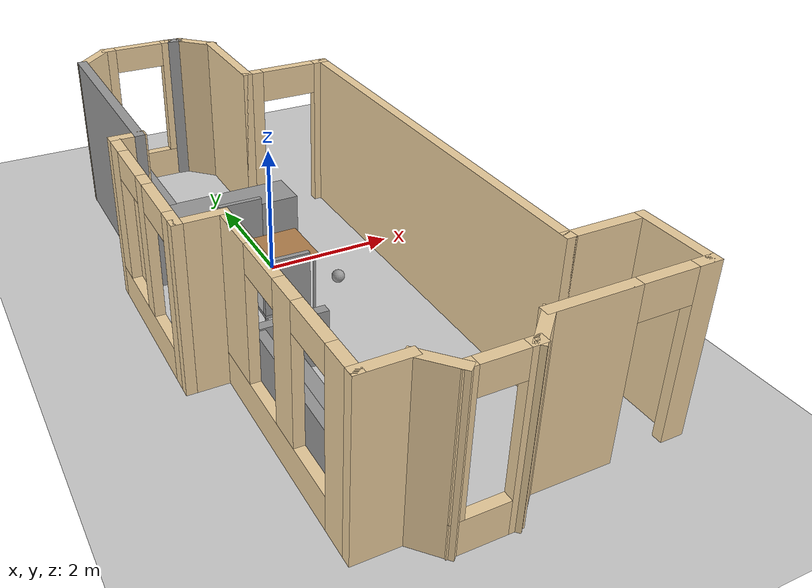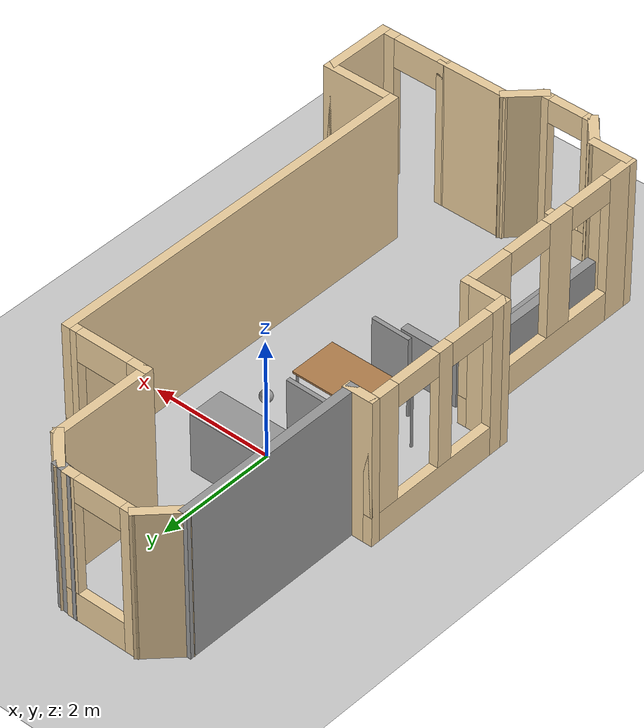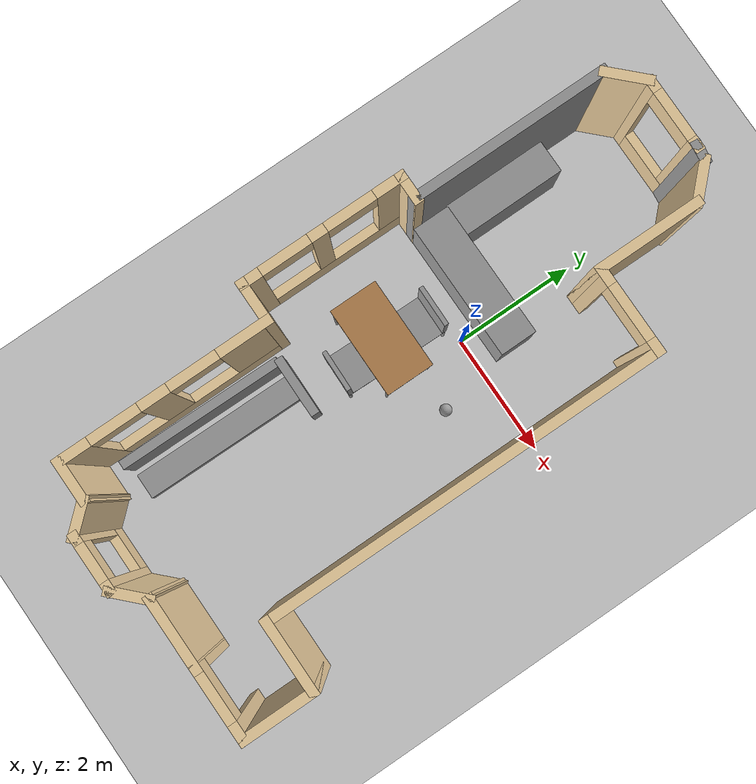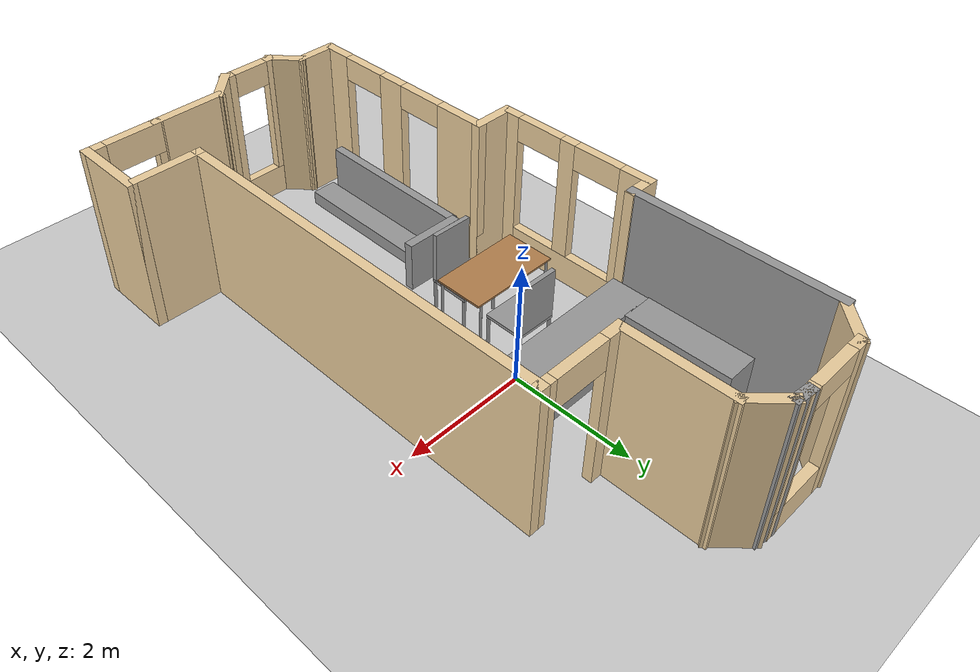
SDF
<sdf version="1.6">
 <world name="default">
  <light name="sun" type="directional">
   <pose>0 0 10 0 -0 0</pose>
   <diffuse>0.8 0.8 0.8 1</diffuse>
   <specular>0.2 0.2 0.2 1</specular>
   <attenuation>
    <range>1000</range>
    <constant>0.9</constant>
    <linear>0.01</linear>
    <quadratic>0.001</quadratic>
   </attenuation>
   <direction>-0.5 0.1 -0.9</direction>
  </light>
  <model name="ground_plane">
   <static>1</static>
   <link name="link">
    <collision name="collision">
     <geometry><plane><normal>0 0 1</normal><size>100 100</size></plane></geometry>
     <surface>
      <contact><collide_bitmask>65535</collide_bitmask></contact>
      <friction><ode><mu>100</mu><mu2>50</mu2></ode></friction>
     </surface>
    </collision>
    <visual name="visual">
     <cast_shadows>0</cast_shadows>
     <geometry><plane><normal>0 0 1</normal><size>100 100</size></plane></geometry>
     <material>
      <script><uri>file://media/materials/scripts/gazebo.material</uri><name>Gazebo/Grey</name></script>
     </material>
    </visual>
   </link>
  </model>
  <gravity>0 0 -9.8</gravity>
  <magnetic_field>6e-06 2.3e-05 -4.2e-05</magnetic_field>
  <atmosphere type="adiabatic"/>
  <physics name="default_physics" default="0" type="ode">
   <max_step_size>0.001</max_step_size>
   <real_time_factor>1</real_time_factor>
   <real_time_update_rate>1000</real_time_update_rate>
  </physics>
  <scene><ambient>0.4 0.4 0.4 1</ambient><background>0.7 0.7 0.7 1</background><shadows>1</shadows></scene>
  <spherical_coordinates>
   <surface_model>EARTH_WGS84</surface_model>
   <latitude_deg>0</latitude_deg>
   <longitude_deg>0</longitude_deg>
   <elevation>0</elevation>
   <heading_deg>0</heading_deg>
  </spherical_coordinates>
  <model name="home_v4">
   <pose>0.364459 -1.06158 0 0 -0 0</pose>
   <link name="Wall_0">
    <collision name="Wall_0_Collision">
     <geometry><box><size>1.25 0.15 2.5</size></box></geometry>
     <pose>0 0 1.25 0 -0 0</pose>
    </collision>
    <visual name="Wall_0_Visual">
     <pose>0 0 1.25 0 -0 0</pose>
     <geometry><box><size>1.25 0.15 2.5</size></box></geometry>
     <material>
      <script><uri>file://media/materials/scripts/gazebo.material</uri><name>Gazebo/Grey</name></script>
      <ambient>0.921569 0.807843 0.615686 1</ambient>
     </material>
     <meta><layer>0</layer></meta>
    </visual>
    <pose>0.840711 -4.55456 0 0 -0 3.14159</pose>
   </link>
   <link name="Wall_10">
    <collision name="Wall_10_Collision">
     <geometry><box><size>0.518694 0.15 2.5</size></box></geometry>
     <pose>0 0 1.25 0 -0 0</pose>
    </collision>
    <visual name="Wall_10_Visual">
     <pose>0 0 1.25 0 -0 0</pose>
     <geometry><box><size>0.518694 0.15 2.5</size></box></geometry>
     <material>
      <script><uri>file://media/materials/scripts/gazebo.material</uri><name>Gazebo/Grey</name></script>
      <ambient>0.921569 0.807843 0.615686 1</ambient>
     </material>
     <meta><layer>0</layer></meta>
    </visual>
    <pose>-2.31992 1.39544 0 0 -0 0</pose>
   </link>
   <link name="Wall_12">
    <collision name="Wall_12_Collision">
     <geometry><box><size>3.25 0.15 2.5</size></box></geometry>
     <pose>0 0 1.25 0 -0 0</pose>
    </collision>
    <visual name="Wall_12_Visual">
     <pose>0 0 1.25 0 -0 0</pose>
     <geometry><box><size>3.25 0.15 2.5</size></box></geometry>
     <material>
      <script><uri>file://media/materials/scripts/gazebo.material</uri><name>Gazebo/Grey</name></script>
      <ambient>1 1 1 1</ambient>
     </material>
     <meta><layer>0</layer></meta>
    </visual>
    <pose>-2.1587 2.94544 0 0 -0 1.5708</pose>
   </link>
   <link name="Wall_14">
    <collision name="Wall_14_Collision">
     <geometry><box><size>0.782712 0.15 2.5</size></box></geometry>
     <pose>0 0 1.25 0 -0 0</pose>
    </collision>
    <visual name="Wall_14_Visual">
     <pose>0 0 1.25 0 -0 0</pose>
     <geometry><box><size>0.782712 0.15 2.5</size></box></geometry>
     <material>
      <script><uri>file://media/materials/scripts/gazebo.material</uri><name>Gazebo/Grey</name></script>
      <ambient>0.921569 0.807843 0.615686 1</ambient>
     </material>
     <meta><layer>0</layer></meta>
    </visual>
    <pose>-1.91187 4.71914 0 0 -0 0.785398</pose>
   </link>
   <link name="Wall_18">
    <pose>-1.11505 4.94283 0 0 -0 0</pose>
    <visual name="Wall_18_Visual_0">
     <pose>-0.508675 0 1.25 0 -0 0</pose>
     <geometry><box><size>0.23265 0.15 2.5</size></box></geometry>
     <material>
      <script><uri>file://media/materials/scripts/gazebo.material</uri><name>Gazebo/Grey</name></script>
      <ambient>0.921569 0.807843 0.615686 1</ambient>
     </material>
     <meta><layer>0</layer></meta>
    </visual>
    <collision name="Wall_18_Collision_0">
     <geometry><box><size>0.23265 0.15 2.5</size></box></geometry>
     <pose>-0.508675 0 1.25 0 -0 0</pose>
    </collision>
    <visual name="Wall_18_Visual_1">
     <pose>0.116325 0 0.25 0 -0 0</pose>
     <geometry><box><size>1.01735 0.15 0.5</size></box></geometry>
     <material>
      <script><uri>file://media/materials/scripts/gazebo.material</uri><name>Gazebo/Grey</name></script>
      <ambient>0.921569 0.807843 0.615686 1</ambient>
     </material>
     <meta><layer>0</layer></meta>
    </visual>
    <collision name="Wall_18_Collision_1">
     <geometry><box><size>1.01735 0.15 0.5</size></box></geometry>
     <pose>0.116325 0 0.25 0 -0 0</pose>
    </collision>
    <visual name="Wall_18_Visual_2">
     <pose>0.516325 0 1.5 0 -0 0</pose>
     <geometry><box><size>0.21735 0.15 2</size></box></geometry>
     <material>
      <script><uri>file://media/materials/scripts/gazebo.material</uri><name>Gazebo/Grey</name></script>
      <ambient>0.921569 0.807843 0.615686 1</ambient>
     </material>
     <meta><layer>0</layer></meta>
    </visual>
    <collision name="Wall_18_Collision_2">
     <geometry><box><size>0.21735 0.15 2</size></box></geometry>
     <pose>0.516325 0 1.5 0 -0 0</pose>
    </collision>
    <visual name="Wall_18_Visual_3">
     <pose>0.00765 0 2.3 0 -0 0</pose>
     <geometry><box><size>0.8 0.15 0.4</size></box></geometry>
     <material>
      <script><uri>file://media/materials/scripts/gazebo.material</uri><name>Gazebo/Grey</name></script>
      <ambient>0.921569 0.807843 0.615686 1</ambient>
     </material>
     <meta><layer>0</layer></meta>
    </visual>
    <collision name="Wall_18_Collision_3">
     <geometry><box><size>0.8 0.15 0.4</size></box></geometry>
     <pose>0.00765 0 2.3 0 -0 0</pose>
    </collision>
   </link>
   <link name="Wall_19">
    <collision name="Wall_19_Collision">
     <geometry><box><size>0.369398 0.15 2.5</size></box></geometry>
     <pose>0 0 1.25 0 -0 0</pose>
    </collision>
    <visual name="Wall_19_Visual">
     <pose>0 0 1.25 0 -0 0</pose>
     <geometry><box><size>0.369398 0.15 2.5</size></box></geometry>
     <material>
      <script><uri>file://media/materials/scripts/gazebo.material</uri><name>Gazebo/Grey</name></script>
      <ambient>1 1 1 1</ambient>
     </material>
     <meta><layer>0</layer></meta>
    </visual>
    <pose>-0.479088 4.93127 0 0 0 -0.105624</pose>
   </link>
   <link name="Wall_2">
    <collision name="Wall_2_Collision">
     <geometry><box><size>0.705255 0.15 2.5</size></box></geometry>
     <pose>0 0 1.25 0 -0 0</pose>
    </collision>
    <visual name="Wall_2_Visual">
     <pose>0 0 1.25 0 -0 0</pose>
     <geometry><box><size>0.705255 0.15 2.5</size></box></geometry>
     <material>
      <script><uri>file://media/materials/scripts/gazebo.material</uri><name>Gazebo/Grey</name></script>
      <ambient>0.921569 0.807843 0.615686 1</ambient>
     </material>
     <meta><layer>0</layer></meta>
    </visual>
    <pose>0.092251 -4.7487 0 0 0 -2.36719</pose>
   </link>
   <link name="Wall_20">
    <collision name="Wall_20_Collision">
     <geometry><box><size>0.75 0.15 2.5</size></box></geometry>
     <pose>0 0 1.25 0 -0 0</pose>
    </collision>
    <visual name="Wall_20_Visual">
     <pose>0 0 1.25 0 -0 0</pose>
     <geometry><box><size>0.75 0.15 2.5</size></box></geometry>
     <material>
      <script><uri>file://media/materials/scripts/gazebo.material</uri><name>Gazebo/Grey</name></script>
      <ambient>0.921569 0.807843 0.615686 1</ambient>
     </material>
     <meta><layer>0</layer></meta>
    </visual>
    <pose>-0.157868 4.70757 0 0 0 -0.785398</pose>
   </link>
   <link name="Wall_21">
    <collision name="Wall_21_Collision">
     <geometry><box><size>1.75 0.15 2.5</size></box></geometry>
     <pose>0 0 1.25 0 -0 0</pose>
    </collision>
    <visual name="Wall_21_Visual">
     <pose>0 0 1.25 0 -0 0</pose>
     <geometry><box><size>1.75 0.15 2.5</size></box></geometry>
     <material>
      <script><uri>file://media/materials/scripts/gazebo.material</uri><name>Gazebo/Grey</name></script>
      <ambient>0.921569 0.807843 0.615686 1</ambient>
     </material>
     <meta><layer>0</layer></meta>
    </visual>
    <pose>0.054264 3.69544 0 0 0 -1.5708</pose>
   </link>
   <link name="Wall_22">
    <pose>0.729264 2.89544 0 0 -0 0</pose>
    <visual name="Wall_22_Visual_0">
     <pose>-0.581037 0 1.25 0 -0 0</pose>
     <geometry><box><size>0.337926 0.15 2.5</size></box></geometry>
     <material>
      <script><uri>file://media/materials/scripts/gazebo.material</uri><name>Gazebo/Grey</name></script>
      <ambient>0.921569 0.807843 0.615686 1</ambient>
     </material>
     <meta><layer>0</layer></meta>
    </visual>
    <collision name="Wall_22_Collision_0">
     <geometry><box><size>0.337926 0.15 2.5</size></box></geometry>
     <pose>-0.581037 0 1.25 0 -0 0</pose>
    </collision>
    <visual name="Wall_22_Visual_1">
     <pose>0.618963 0 1.25 0 -0 0</pose>
     <geometry><box><size>0.262074 0.15 2.5</size></box></geometry>
     <material>
      <script><uri>file://media/materials/scripts/gazebo.material</uri><name>Gazebo/Grey</name></script>
      <ambient>0.921569 0.807843 0.615686 1</ambient>
     </material>
     <meta><layer>0</layer></meta>
    </visual>
    <collision name="Wall_22_Collision_1">
     <geometry><box><size>0.262074 0.15 2.5</size></box></geometry>
     <pose>0.618963 0 1.25 0 -0 0</pose>
    </collision>
    <visual name="Wall_22_Visual_2">
     <pose>0.037926 0 2.25 0 -0 0</pose>
     <geometry><box><size>0.9 0.15 0.5</size></box></geometry>
     <material>
      <script><uri>file://media/materials/scripts/gazebo.material</uri><name>Gazebo/Grey</name></script>
      <ambient>0.921569 0.807843 0.615686 1</ambient>
     </material>
     <meta><layer>0</layer></meta>
    </visual>
    <collision name="Wall_22_Collision_2">
     <geometry><box><size>0.9 0.15 0.5</size></box></geometry>
     <pose>0.037926 0 2.25 0 -0 0</pose>
    </collision>
   </link>
   <link name="Wall_24">
    <collision name="Wall_24_Collision">
     <geometry><box><size>6.5 0.15 2.5</size></box></geometry>
     <pose>0 0 1.25 0 -0 0</pose>
    </collision>
    <visual name="Wall_24_Visual">
     <pose>0 0 1.25 0 -0 0</pose>
     <geometry><box><size>6.5 0.15 2.5</size></box></geometry>
     <material>
      <script><uri>file://media/materials/scripts/gazebo.material</uri><name>Gazebo/Grey</name></script>
      <ambient>0.921569 0.807843 0.615686 1</ambient>
     </material>
     <meta><layer>0</layer></meta>
    </visual>
    <pose>1.40426 -0.279559 0 0 0 -1.5708</pose>
   </link>
   <link name="Wall_25">
    <collision name="Wall_25_Collision">
     <geometry><box><size>1.25 0.15 2.5</size></box></geometry>
     <pose>0 0 1.25 0 -0 0</pose>
    </collision>
    <visual name="Wall_25_Visual">
     <pose>0 0 1.25 0 -0 0</pose>
     <geometry><box><size>1.25 0.15 2.5</size></box></geometry>
     <material>
      <script><uri>file://media/materials/scripts/gazebo.material</uri><name>Gazebo/Grey</name></script>
      <ambient>0.921569 0.807843 0.615686 1</ambient>
     </material>
     <meta><layer>0</layer></meta>
    </visual>
    <pose>1.95426 -3.45456 0 0 -0 0</pose>
   </link>
   <link name="Wall_27">
    <collision name="Wall_27_Collision">
     <geometry><box><size>1.25 0.15 2.5</size></box></geometry>
     <pose>0 0 1.25 0 -0 0</pose>
    </collision>
    <visual name="Wall_27_Visual">
     <pose>0 0 1.25 0 -0 0</pose>
     <geometry><box><size>1.25 0.15 2.5</size></box></geometry>
     <material>
      <script><uri>file://media/materials/scripts/gazebo.material</uri><name>Gazebo/Grey</name></script>
      <ambient>0.921569 0.807843 0.615686 1</ambient>
     </material>
     <meta><layer>0</layer></meta>
    </visual>
    <pose>2.50426 -4.00456 0 0 0 -1.5708</pose>
   </link>
   <link name="Wall_28">
    <pose>1.94749 -4.55456 0 0 -0 3.14159</pose>
    <visual name="Wall_28_Visual_0">
     <pose>-0.463636 0 1.25 0 -0 0</pose>
     <geometry><box><size>0.336282 0.15 2.5</size></box></geometry>
     <material>
      <script><uri>file://media/materials/scripts/gazebo.material</uri><name>Gazebo/Grey</name></script>
      <ambient>0.921569 0.807843 0.615686 1</ambient>
     </material>
     <meta><layer>0</layer></meta>
    </visual>
    <collision name="Wall_28_Collision_0">
     <geometry><box><size>0.336282 0.15 2.5</size></box></geometry>
     <pose>-0.463636 0 1.25 0 -0 0</pose>
    </collision>
    <visual name="Wall_28_Visual_1">
     <pose>0.618141 0 1.25 0 -0 0</pose>
     <geometry><box><size>0.027271 0.15 2.5</size></box></geometry>
     <material>
      <script><uri>file://media/materials/scripts/gazebo.material</uri><name>Gazebo/Grey</name></script>
      <ambient>0.921569 0.807843 0.615686 1</ambient>
     </material>
     <meta><layer>0</layer></meta>
    </visual>
    <collision name="Wall_28_Collision_1">
     <geometry><box><size>0.027271 0.15 2.5</size></box></geometry>
     <pose>0.618141 0 1.25 0 -0 0</pose>
    </collision>
    <visual name="Wall_28_Visual_2">
     <pose>0.154505 0 2.25 0 -0 0</pose>
     <geometry><box><size>0.9 0.15 0.5</size></box></geometry>
     <material>
      <script><uri>file://media/materials/scripts/gazebo.material</uri><name>Gazebo/Grey</name></script>
      <ambient>0.921569 0.807843 0.615686 1</ambient>
     </material>
     <meta><layer>0</layer></meta>
    </visual>
    <collision name="Wall_28_Collision_2">
     <geometry><box><size>0.9 0.15 0.5</size></box></geometry>
     <pose>0.154505 0 2.25 0 -0 0</pose>
    </collision>
   </link>
   <link name="Wall_3">
    <pose>-0.531209 -4.92273 0 0 -0 3.14159</pose>
    <visual name="Wall_3_Visual_0">
     <pose>-0.395508 0 1.25 0 -0 0</pose>
     <geometry><box><size>0.208983 0.15 2.5</size></box></geometry>
     <material>
      <script><uri>file://media/materials/scripts/gazebo.material</uri><name>Gazebo/Grey</name></script>
      <ambient>0.921569 0.807843 0.615686 1</ambient>
     </material>
     <meta><layer>0</layer></meta>
    </visual>
    <collision name="Wall_3_Collision_0">
     <geometry><box><size>0.208983 0.15 2.5</size></box></geometry>
     <pose>-0.395508 0 1.25 0 -0 0</pose>
    </collision>
    <visual name="Wall_3_Visual_1">
     <pose>0.104492 0 0.25 0 -0 0</pose>
     <geometry><box><size>0.791017 0.15 0.5</size></box></geometry>
     <material>
      <script><uri>file://media/materials/scripts/gazebo.material</uri><name>Gazebo/Grey</name></script>
      <ambient>0.921569 0.807843 0.615686 1</ambient>
     </material>
     <meta><layer>0</layer></meta>
    </visual>
    <collision name="Wall_3_Collision_1">
     <geometry><box><size>0.791017 0.15 0.5</size></box></geometry>
     <pose>0.104492 0 0.25 0 -0 0</pose>
    </collision>
    <visual name="Wall_3_Visual_2">
     <pose>0.404492 0 1.5 0 -0 0</pose>
     <geometry><box><size>0.191017 0.15 2</size></box></geometry>
     <material>
      <script><uri>file://media/materials/scripts/gazebo.material</uri><name>Gazebo/Grey</name></script>
      <ambient>0.921569 0.807843 0.615686 1</ambient>
     </material>
     <meta><layer>0</layer></meta>
    </visual>
    <collision name="Wall_3_Collision_2">
     <geometry><box><size>0.191017 0.15 2</size></box></geometry>
     <pose>0.404492 0 1.5 0 -0 0</pose>
    </collision>
    <visual name="Wall_3_Visual_3">
     <pose>0.008983 0 2.3 0 -0 0</pose>
     <geometry><box><size>0.6 0.15 0.4</size></box></geometry>
     <material>
      <script><uri>file://media/materials/scripts/gazebo.material</uri><name>Gazebo/Grey</name></script>
      <ambient>0.921569 0.807843 0.615686 1</ambient>
     </material>
     <meta><layer>0</layer></meta>
    </visual>
    <collision name="Wall_3_Collision_3">
     <geometry><box><size>0.6 0.15 0.4</size></box></geometry>
     <pose>0.008983 0 2.3 0 -0 0</pose>
    </collision>
   </link>
   <link name="Wall_4">
    <collision name="Wall_4_Collision">
     <geometry><box><size>0.671446 0.15 2.5</size></box></geometry>
     <pose>0 0 1.25 0 -0 0</pose>
    </collision>
    <visual name="Wall_4_Visual">
     <pose>0 0 1.25 0 -0 0</pose>
     <geometry><box><size>0.671446 0.15 2.5</size></box></geometry>
     <material>
      <script><uri>file://media/materials/scripts/gazebo.material</uri><name>Gazebo/Grey</name></script>
      <ambient>0.921569 0.807843 0.615686 1</ambient>
     </material>
     <meta><layer>0</layer></meta>
    </visual>
    <pose>-1.13024 -4.7487 0 0 -0 2.30162</pose>
   </link>
   <link name="Wall_5">
    <collision name="Wall_5_Collision">
     <geometry><box><size>0.75 0.15 2.5</size></box></geometry>
     <pose>0 0 1.25 0 -0 0</pose>
    </collision>
    <visual name="Wall_5_Visual">
     <pose>0 0 1.25 0 -0 0</pose>
     <geometry><box><size>0.75 0.15 2.5</size></box></geometry>
     <material>
      <script><uri>file://media/materials/scripts/gazebo.material</uri><name>Gazebo/Grey</name></script>
      <ambient>0.921569 0.807843 0.615686 1</ambient>
     </material>
     <meta><layer>0</layer></meta>
    </visual>
    <pose>-1.60426 -4.55456 0 0 -0 3.14159</pose>
   </link>
   <link name="Wall_6">
    <pose>-1.90426 -2.87956 0 0 -0 1.5708</pose>
    <visual name="Wall_6_Visual_0">
     <pose>-1.47 0 1.25 0 -0 0</pose>
     <geometry><box><size>0.559997 0.15 2.5</size></box></geometry>
     <material>
      <script><uri>file://media/materials/scripts/gazebo.material</uri><name>Gazebo/Grey</name></script>
      <ambient>0.921569 0.807843 0.615686 1</ambient>
     </material>
     <meta><layer>0</layer></meta>
    </visual>
    <collision name="Wall_6_Collision_0">
     <geometry><box><size>0.559997 0.15 2.5</size></box></geometry>
     <pose>-1.47 0 1.25 0 -0 0</pose>
    </collision>
    <visual name="Wall_6_Visual_1">
     <pose>0.279999 0 0.25 0 -0 0</pose>
     <geometry><box><size>2.94 0.15 0.5</size></box></geometry>
     <material>
      <script><uri>file://media/materials/scripts/gazebo.material</uri><name>Gazebo/Grey</name></script>
      <ambient>0.921569 0.807843 0.615686 1</ambient>
     </material>
     <meta><layer>0</layer></meta>
    </visual>
    <collision name="Wall_6_Collision_1">
     <geometry><box><size>2.94 0.15 0.5</size></box></geometry>
     <pose>0.279999 0 0.25 0 -0 0</pose>
    </collision>
    <visual name="Wall_6_Visual_2">
     <pose>-0.156425 0 1.5 0 -0 0</pose>
     <geometry><box><size>0.467155 0.15 2</size></box></geometry>
     <material>
      <script><uri>file://media/materials/scripts/gazebo.material</uri><name>Gazebo/Grey</name></script>
      <ambient>0.921569 0.807843 0.615686 1</ambient>
     </material>
     <meta><layer>0</layer></meta>
    </visual>
    <collision name="Wall_6_Collision_2">
     <geometry><box><size>0.467155 0.15 2</size></box></geometry>
     <pose>-0.156425 0 1.5 0 -0 0</pose>
    </collision>
    <visual name="Wall_6_Visual_3">
     <pose>1.31358 0 1.5 0 -0 0</pose>
     <geometry><box><size>0.872848 0.15 2</size></box></geometry>
     <material>
      <script><uri>file://media/materials/scripts/gazebo.material</uri><name>Gazebo/Grey</name></script>
      <ambient>0.921569 0.807843 0.615686 1</ambient>
     </material>
     <meta><layer>0</layer></meta>
    </visual>
    <collision name="Wall_6_Collision_3">
     <geometry><box><size>0.872848 0.15 2</size></box></geometry>
     <pose>1.31358 0 1.5 0 -0 0</pose>
    </collision>
    <visual name="Wall_6_Visual_4">
     <pose>-0.790003 0 2.3 0 -0 0</pose>
     <geometry><box><size>0.8 0.15 0.4</size></box></geometry>
     <material>
      <script><uri>file://media/materials/scripts/gazebo.material</uri><name>Gazebo/Grey</name></script>
      <ambient>0.921569 0.807843 0.615686 1</ambient>
     </material>
     <meta><layer>0</layer></meta>
    </visual>
    <collision name="Wall_6_Collision_4">
     <geometry><box><size>0.8 0.15 0.4</size></box></geometry>
     <pose>-0.790003 0 2.3 0 -0 0</pose>
    </collision>
    <visual name="Wall_6_Visual_5">
     <pose>0.477152 0 2.3 0 -0 0</pose>
     <geometry><box><size>0.8 0.15 0.4</size></box></geometry>
     <material>
      <script><uri>file://media/materials/scripts/gazebo.material</uri><name>Gazebo/Grey</name></script>
      <ambient>0.921569 0.807843 0.615686 1</ambient>
     </material>
     <meta><layer>0</layer></meta>
    </visual>
    <collision name="Wall_6_Collision_5">
     <geometry><box><size>0.8 0.15 0.4</size></box></geometry>
     <pose>0.477152 0 2.3 0 -0 0</pose>
    </collision>
   </link>
   <link name="Wall_8">
    <collision name="Wall_8_Collision">
     <geometry><box><size>0.75 0.15 2.5</size></box></geometry>
     <pose>0 0 1.25 0 -0 0</pose>
    </collision>
    <visual name="Wall_8_Visual">
     <pose>0 0 1.25 0 -0 0</pose>
     <geometry><box><size>0.75 0.15 2.5</size></box></geometry>
     <material>
      <script><uri>file://media/materials/scripts/gazebo.material</uri><name>Gazebo/Grey</name></script>
      <ambient>0.921569 0.807843 0.615686 1</ambient>
     </material>
     <meta><layer>0</layer></meta>
    </visual>
    <pose>-2.20426 -1.20456 0 0 -0 3.14159</pose>
   </link>
   <link name="Wall_9">
    <pose>-2.50426 0.095441 0 0 -0 1.5708</pose>
    <visual name="Wall_9_Visual_0">
     <pose>-1.19109 0 1.25 0 -0 0</pose>
     <geometry><box><size>0.367828 0.15 2.5</size></box></geometry>
     <material>
      <script><uri>file://media/materials/scripts/gazebo.material</uri><name>Gazebo/Grey</name></script>
      <ambient>0.921569 0.807843 0.615686 1</ambient>
     </material>
     <meta><layer>0</layer></meta>
    </visual>
    <collision name="Wall_9_Collision_0">
     <geometry><box><size>0.367828 0.15 2.5</size></box></geometry>
     <pose>-1.19109 0 1.25 0 -0 0</pose>
    </collision>
    <visual name="Wall_9_Visual_1">
     <pose>0.183914 0 0.25 0 -0 0</pose>
     <geometry><box><size>2.38217 0.15 0.5</size></box></geometry>
     <material>
      <script><uri>file://media/materials/scripts/gazebo.material</uri><name>Gazebo/Grey</name></script>
      <ambient>0.921569 0.807843 0.615686 1</ambient>
     </material>
     <meta><layer>0</layer></meta>
    </visual>
    <collision name="Wall_9_Collision_1">
     <geometry><box><size>2.38217 0.15 0.5</size></box></geometry>
     <pose>0.183914 0 0.25 0 -0 0</pose>
    </collision>
    <visual name="Wall_9_Visual_2">
     <pose>-0.074162 0 1.5 0 -0 0</pose>
     <geometry><box><size>0.266019 0.15 2</size></box></geometry>
     <material>
      <script><uri>file://media/materials/scripts/gazebo.material</uri><name>Gazebo/Grey</name></script>
      <ambient>0.921569 0.807843 0.615686 1</ambient>
     </material>
     <meta><layer>0</layer></meta>
    </visual>
    <collision name="Wall_9_Collision_2">
     <geometry><box><size>0.266019 0.15 2</size></box></geometry>
     <pose>-0.074162 0 1.5 0 -0 0</pose>
    </collision>
    <visual name="Wall_9_Visual_3">
     <pose>1.11692 0 1.5 0 -0 0</pose>
     <geometry><box><size>0.516153 0.15 2</size></box></geometry>
     <material>
      <script><uri>file://media/materials/scripts/gazebo.material</uri><name>Gazebo/Grey</name></script>
      <ambient>0.921569 0.807843 0.615686 1</ambient>
     </material>
     <meta><layer>0</layer></meta>
    </visual>
    <collision name="Wall_9_Collision_3">
     <geometry><box><size>0.516153 0.15 2</size></box></geometry>
     <pose>1.11692 0 1.5 0 -0 0</pose>
    </collision>
    <visual name="Wall_9_Visual_4">
     <pose>-0.607172 0 2.3 0 -0 0</pose>
     <geometry><box><size>0.8 0.15 0.4</size></box></geometry>
     <material>
      <script><uri>file://media/materials/scripts/gazebo.material</uri><name>Gazebo/Grey</name></script>
      <ambient>0.921569 0.807843 0.615686 1</ambient>
     </material>
     <meta><layer>0</layer></meta>
    </visual>
    <collision name="Wall_9_Collision_4">
     <geometry><box><size>0.8 0.15 0.4</size></box></geometry>
     <pose>-0.607172 0 2.3 0 -0 0</pose>
    </collision>
    <visual name="Wall_9_Visual_5">
     <pose>0.458847 0 2.3 0 -0 0</pose>
     <geometry><box><size>0.8 0.15 0.4</size></box></geometry>
     <material>
      <script><uri>file://media/materials/scripts/gazebo.material</uri><name>Gazebo/Grey</name></script>
      <ambient>0.921569 0.807843 0.615686 1</ambient>
     </material>
     <meta><layer>0</layer></meta>
    </visual>
    <collision name="Wall_9_Collision_5">
     <geometry><box><size>0.8 0.15 0.4</size></box></geometry>
     <pose>0.458847 0 2.3 0 -0 0</pose>
    </collision>
   </link>
   <static>1</static>
  </model>
  <model name="couch">
   <link name="link_0">
    <pose>-1.19145 -4.17235 0.583935 0 -0 0</pose>
    <inertial>
     <mass>0.33429</mass>
     <inertia>
      <ixx>0.232533</ixx>
      <ixy>0</ixy>
      <ixz>0</ixz>
      <iyy>0.0199772</iyy>
      <iyz>0</iyz>
      <izz>0.213725</izz>
     </inertia>
    </inertial>
    <visual name="visual">
     <geometry><box><size>0.14485 2.76606 0.834351</size></box></geometry>
     <material>
      <lighting>1</lighting>
      <script><uri>file://media/materials/scripts/gazebo.material</uri><name>Gazebo/Grey</name></script>
      <shader type="pixel"><normal_map>__default__</normal_map></shader>
      <ambient>0.3 0.3 0.3 1</ambient>
      <diffuse>0.7 0.7 0.7 1</diffuse>
      <specular>0.01 0.01 0.01 1</specular>
      <emissive>0 0 0 1</emissive>
     </material>
    </visual>
    <collision name="collision">
     <geometry><box><size>0.14485 2.76606 0.834351</size></box></geometry>
     <surface>
      <friction>
       <ode><mu>1</mu><mu2>1</mu2><fdir1>0 0 0</fdir1><slip1>0</slip1><slip2>0</slip2></ode>
       <torsional>
        <coefficient>1</coefficient>
        <patch_radius>0</patch_radius>
        <surface_radius>0</surface_radius>
        <use_patch_radius>1</use_patch_radius>
        <ode><slip>0</slip></ode>
       </torsional>
      </friction>
      <bounce><restitution_coefficient>0</restitution_coefficient><threshold>1e+06</threshold></bounce>
      <contact>
       <collide_without_contact>0</collide_without_contact>
       <collide_without_contact_bitmask>1</collide_without_contact_bitmask>
       <collide_bitmask>1</collide_bitmask>
       <ode>
        <soft_cfm>0</soft_cfm>
        <soft_erp>0.2</soft_erp>
        <kp>1e+13</kp>
        <kd>1</kd>
        <max_vel>0.01</max_vel>
        <min_depth>0</min_depth>
       </ode>
       <bullet>
        <split_impulse>1</split_impulse>
        <split_impulse_penetration_threshold>-0.01</split_impulse_penetration_threshold>
        <soft_cfm>0</soft_cfm>
        <soft_erp>0.2</soft_erp>
        <kp>1e+13</kp>
        <kd>1</kd>
       </bullet>
      </contact>
     </surface>
    </collision>
   </link>
   <link name="link_2">
    <pose>-0.806417 -4.15963 0.280513 0 -0 0</pose>
    <inertial>
     <mass>0.174926</mass>
     <inertia>
      <ixx>0.112278</ixx>
      <ixy>0</ixy>
      <ixz>0</ixz>
      <iyy>0.00327316</iyy>
      <iyz>0</iyz>
      <izz>0.114057</izz>
     </inertia>
    </inertial>
    <visual name="visual">
     <geometry><box><size>0.416255 2.76606 0.226434</size></box></geometry>
     <material>
      <lighting>1</lighting>
      <script><uri>file://media/materials/scripts/gazebo.material</uri><name>Gazebo/Grey</name></script>
      <shader type="pixel"><normal_map>__default__</normal_map></shader>
      <ambient>0.3 0.3 0.3 1</ambient>
      <diffuse>0.7 0.7 0.7 1</diffuse>
      <specular>0.01 0.01 0.01 1</specular>
      <emissive>0 0 0 1</emissive>
     </material>
    </visual>
    <collision name="collision">
     <geometry><box><size>0.416255 2.76606 0.226434</size></box></geometry>
     <surface>
      <friction>
       <ode><mu>1</mu><mu2>1</mu2><fdir1>0 0 0</fdir1><slip1>0</slip1><slip2>0</slip2></ode>
       <torsional>
        <coefficient>1</coefficient>
        <patch_radius>0</patch_radius>
        <surface_radius>0</surface_radius>
        <use_patch_radius>1</use_patch_radius>
        <ode><slip>0</slip></ode>
       </torsional>
      </friction>
      <bounce><restitution_coefficient>0</restitution_coefficient><threshold>1e+06</threshold></bounce>
      <contact>
       <collide_without_contact>0</collide_without_contact>
       <collide_without_contact_bitmask>1</collide_without_contact_bitmask>
       <collide_bitmask>1</collide_bitmask>
       <ode>
        <soft_cfm>0</soft_cfm>
        <soft_erp>0.2</soft_erp>
        <kp>1e+13</kp>
        <kd>1</kd>
        <max_vel>0.01</max_vel>
        <min_depth>0</min_depth>
       </ode>
       <bullet>
        <split_impulse>1</split_impulse>
        <split_impulse_penetration_threshold>-0.01</split_impulse_penetration_threshold>
        <soft_cfm>0</soft_cfm>
        <soft_erp>0.2</soft_erp>
        <kp>1e+13</kp>
        <kd>1</kd>
       </bullet>
      </contact>
     </surface>
    </collision>
   </link>
   <link name="link_3">
    <pose>-0.724044 -2.77007 0.606187 0 -0 0</pose>
    <inertial>
     <mass>0.172557</mass>
     <inertia>
      <ixx>0.00921711</ixx>
      <ixy>0</ixy>
      <ixz>0</ixz>
      <iyy>0.0232951</iyy>
      <iyz>0</iyz>
      <izz>0.0146814</izz>
     </inertia>
    </inertial>
    <visual name="visual">
     <geometry><box><size>1 0.14485 0.834351</size></box></geometry>
     <material>
      <lighting>1</lighting>
      <script><uri>file://media/materials/scripts/gazebo.material</uri><name>Gazebo/Grey</name></script>
      <shader type="pixel"><normal_map>__default__</normal_map></shader>
      <ambient>0.3 0.3 0.3 1</ambient>
      <diffuse>0.7 0.7 0.7 1</diffuse>
      <specular>0.01 0.01 0.01 1</specular>
      <emissive>0 0 0 1</emissive>
     </material>
    </visual>
    <collision name="collision">
     <geometry><box><size>1 0.14485 0.834351</size></box></geometry>
     <surface>
      <friction>
       <ode><mu>1</mu><mu2>1</mu2><fdir1>0 0 0</fdir1><slip1>0</slip1><slip2>0</slip2></ode>
       <torsional>
        <coefficient>1</coefficient>
        <patch_radius>0</patch_radius>
        <surface_radius>0</surface_radius>
        <use_patch_radius>1</use_patch_radius>
        <ode><slip>0</slip></ode>
       </torsional>
      </friction>
      <bounce><restitution_coefficient>0</restitution_coefficient><threshold>1e+06</threshold></bounce>
      <contact>
       <collide_without_contact>0</collide_without_contact>
       <collide_without_contact_bitmask>1</collide_without_contact_bitmask>
       <collide_bitmask>1</collide_bitmask>
       <ode>
        <soft_cfm>0</soft_cfm>
        <soft_erp>0.2</soft_erp>
        <kp>1e+13</kp>
        <kd>1</kd>
        <max_vel>0.01</max_vel>
        <min_depth>0</min_depth>
       </ode>
       <bullet>
        <split_impulse>1</split_impulse>
        <split_impulse_penetration_threshold>-0.01</split_impulse_penetration_threshold>
        <soft_cfm>0</soft_cfm>
        <soft_erp>0.2</soft_erp>
        <kp>1e+13</kp>
        <kd>1</kd>
       </bullet>
      </contact>
     </surface>
    </collision>
   </link>
   <joint name="link_0_JOINT_0" type="fixed">
    <parent>link_0</parent>
    <child>link_2</child>
    <physics>
     <ode><limit><cfm>0</cfm><erp>0.2</erp></limit><suspension><cfm>0</cfm><erp>0.2</erp></suspension></ode>
    </physics>
   </joint>
   <joint name="link_0_JOINT_1" type="fixed">
    <parent>link_0</parent>
    <child>link_3</child>
    <physics>
     <ode><limit><cfm>0</cfm><erp>0.2</erp></limit><suspension><cfm>0</cfm><erp>0.2</erp></suspension></ode>
    </physics>
   </joint>
   <static>0</static>
   <pose>-0.025273 0.299837 -0.167913 -0 0.001026 -0.008569</pose>
  </model>
  <model name="Counter_Top">
   <link name="link_4">
    <pose>0.154773 0.032272 0 0 -0 0</pose>
    <inertial>
     <mass>1.37733</mass>
     <inertia>
      <ixx>0.157254</ixx>
      <ixy>0</ixy>
      <ixz>0</ixz>
      <iyy>0.703133</iyy>
      <iyz>0</iyz>
      <izz>0.630831</izz>
     </inertia>
    </inertial>
    <visual name="visual">
     <geometry><box><size>2.26408 0.608339 1</size></box></geometry>
     <material>
      <lighting>1</lighting>
      <script><uri>file://media/materials/scripts/gazebo.material</uri><name>Gazebo/Grey</name></script>
      <shader type="pixel"><normal_map>__default__</normal_map></shader>
      <ambient>0.3 0.3 0.3 1</ambient>
      <diffuse>0.7 0.7 0.7 1</diffuse>
      <specular>0.01 0.01 0.01 1</specular>
      <emissive>0 0 0 1</emissive>
     </material>
    </visual>
    <collision name="collision">
     <geometry><box><size>2.26408 0.608339 1</size></box></geometry>
     <surface>
      <friction>
       <ode><mu>1</mu><mu2>1</mu2><fdir1>0 0 0</fdir1><slip1>0</slip1><slip2>0</slip2></ode>
       <torsional>
        <coefficient>1</coefficient>
        <patch_radius>0</patch_radius>
        <surface_radius>0</surface_radius>
        <use_patch_radius>1</use_patch_radius>
        <ode><slip>0</slip></ode>
       </torsional>
      </friction>
      <bounce><restitution_coefficient>0</restitution_coefficient><threshold>1e+06</threshold></bounce>
      <contact>
       <collide_without_contact>0</collide_without_contact>
       <collide_without_contact_bitmask>1</collide_without_contact_bitmask>
       <collide_bitmask>1</collide_bitmask>
       <ode>
        <soft_cfm>0</soft_cfm>
        <soft_erp>0.2</soft_erp>
        <kp>1e+13</kp>
        <kd>1</kd>
        <max_vel>0.01</max_vel>
        <min_depth>0</min_depth>
       </ode>
       <bullet>
        <split_impulse>1</split_impulse>
        <split_impulse_penetration_threshold>-0.01</split_impulse_penetration_threshold>
        <soft_cfm>0</soft_cfm>
        <soft_erp>0.2</soft_erp>
        <kp>1e+13</kp>
        <kd>1</kd>
       </bullet>
      </contact>
     </surface>
    </collision>
   </link>
   <link name="link_5">
    <pose>-0.726732 1.17428 0 0 -0 0</pose>
    <inertial>
     <mass>0.9068</mass>
     <inertia>
      <ixx>0.295862</ixx>
      <ixy>0</ixy>
      <ixz>0</ixz>
      <iyy>0.0968837</iyy>
      <iyz>0</iyz>
      <izz>0.241613</izz>
     </inertia>
    </inertial>
    <visual name="visual">
     <geometry><box><size>0.531127 1.70741 1</size></box></geometry>
     <material>
      <lighting>1</lighting>
      <script><uri>file://media/materials/scripts/gazebo.material</uri><name>Gazebo/Grey</name></script>
      <shader type="pixel"/>
      <ambient>0.3 0.3 0.3 1</ambient>
      <diffuse>0.7 0.7 0.7 1</diffuse>
      <specular>0.01 0.01 0.01 1</specular>
      <emissive>0 0 0 1</emissive>
     </material>
    </visual>
    <collision name="collision">
     <geometry><box><size>0.531127 1.70741 1</size></box></geometry>
     <surface>
      <friction>
       <ode><mu>1</mu><mu2>1</mu2><fdir1>0 0 0</fdir1><slip1>0</slip1><slip2>0</slip2></ode>
       <torsional>
        <coefficient>1</coefficient>
        <patch_radius>0</patch_radius>
        <surface_radius>0</surface_radius>
        <use_patch_radius>1</use_patch_radius>
        <ode><slip>0</slip></ode>
       </torsional>
      </friction>
      <bounce><restitution_coefficient>0</restitution_coefficient><threshold>1e+06</threshold></bounce>
      <contact>
       <collide_without_contact>0</collide_without_contact>
       <collide_without_contact_bitmask>1</collide_without_contact_bitmask>
       <collide_bitmask>1</collide_bitmask>
       <ode>
        <soft_cfm>0</soft_cfm>
        <soft_erp>0.2</soft_erp>
        <kp>1e+13</kp>
        <kd>1</kd>
        <max_vel>0.01</max_vel>
        <min_depth>0</min_depth>
       </ode>
       <bullet>
        <split_impulse>1</split_impulse>
        <split_impulse_penetration_threshold>-0.01</split_impulse_penetration_threshold>
        <soft_cfm>0</soft_cfm>
        <soft_erp>0.2</soft_erp>
        <kp>1e+13</kp>
        <kd>1</kd>
       </bullet>
      </contact>
     </surface>
    </collision>
   </link>
   <joint name="link_4_JOINT_2" type="fixed">
    <parent>link_4</parent>
    <child>link_5</child>
    <physics>
     <ode><limit><cfm>0</cfm><erp>0.2</erp></limit><suspension><cfm>0</cfm><erp>0.2</erp></suspension></ode>
    </physics>
   </joint>
   <static>0</static>
   <pose>-0.719321 0.539813 0.5 0 -0 0.003683</pose>
  </model>
  <model name="table">
   <static>1</static>
   <link name="link">
    <collision name="surface">
     <pose>0 0 1 0 -0 0</pose>
     <geometry><box><size>1.5 0.8 0.03</size></box></geometry>
     <surface><friction><ode><mu>0.6</mu><mu2>0.6</mu2></ode></friction></surface>
    </collision>
    <visual name="visual1">
     <pose>0 0 1 0 -0 0</pose>
     <geometry><box><size>1.5 0.8 0.03</size></box></geometry>
     <material>
      <script><uri>file://media/materials/scripts/gazebo.material</uri><name>Gazebo/Wood</name></script>
     </material>
    </visual>
    <collision name="front_left_leg">
     <pose>0.68 0.38 0.5 0 -0 0</pose>
     <geometry><cylinder><radius>0.02</radius><length>1</length></cylinder></geometry>
    </collision>
    <visual name="front_left_leg">
     <pose>0.68 0.38 0.5 0 -0 0</pose>
     <geometry><cylinder><radius>0.02</radius><length>1</length></cylinder></geometry>
     <material>
      <script><uri>file://media/materials/scripts/gazebo.material</uri><name>Gazebo/Grey</name></script>
     </material>
    </visual>
    <collision name="front_right_leg">
     <pose>0.68 -0.38 0.5 0 -0 0</pose>
     <geometry><cylinder><radius>0.02</radius><length>1</length></cylinder></geometry>
    </collision>
    <visual name="front_right_leg">
     <pose>0.68 -0.38 0.5 0 -0 0</pose>
     <geometry><cylinder><radius>0.02</radius><length>1</length></cylinder></geometry>
     <material>
      <script><uri>file://media/materials/scripts/gazebo.material</uri><name>Gazebo/Grey</name></script>
     </material>
    </visual>
    <collision name="back_right_leg">
     <pose>-0.68 -0.38 0.5 0 -0 0</pose>
     <geometry><cylinder><radius>0.02</radius><length>1</length></cylinder></geometry>
    </collision>
    <visual name="back_right_leg">
     <pose>-0.68 -0.38 0.5 0 -0 0</pose>
     <geometry><cylinder><radius>0.02</radius><length>1</length></cylinder></geometry>
     <material>
      <script><uri>file://media/materials/scripts/gazebo.material</uri><name>Gazebo/Grey</name></script>
     </material>
    </visual>
    <collision name="back_left_leg">
     <pose>-0.68 0.38 0.5 0 -0 0</pose>
     <geometry><cylinder><radius>0.02</radius><length>1</length></cylinder></geometry>
    </collision>
    <visual name="back_left_leg">
     <pose>-0.68 0.38 0.5 0 -0 0</pose>
     <geometry><cylinder><radius>0.02</radius><length>1</length></cylinder></geometry>
     <material>
      <script><uri>file://media/materials/scripts/gazebo.material</uri><name>Gazebo/Grey</name></script>
     </material>
    </visual>
   </link>
   <pose>-0.635873 -1.04074 0 0 -0 0</pose>
  </model>
  <model name="chair2_clone">
   <link name="link_12">
    <pose>0.315657 -2.84973 0.453284 0 -0 0</pose>
    <inertial>
     <mass>0.0218595</mass>
     <inertia>
      <ixx>0.00079758</ixx>
      <ixy>0</ixy>
      <ixz>0</ixz>
      <iyy>0.00079758</iyy>
      <iyz>0</iyz>
      <izz>0.001587</izz>
     </inertia>
    </inertial>
    <visual name="visual">
     <geometry><box><size>0.66 0.66 0.047346</size></box></geometry>
     <material>
      <lighting>1</lighting>
      <script><uri>file://media/materials/scripts/gazebo.material</uri><name>Gazebo/Grey</name></script>
      <shader type="pixel"><normal_map>__default__</normal_map></shader>
      <ambient>0.3 0.3 0.3 1</ambient>
      <diffuse>0.7 0.7 0.7 1</diffuse>
      <specular>0.01 0.01 0.01 1</specular>
      <emissive>0 0 0 1</emissive>
     </material>
    </visual>
    <collision name="collision">
     <geometry><box><size>0.66 0.66 0.047346</size></box></geometry>
     <surface>
      <friction>
       <ode><mu>1</mu><mu2>1</mu2><fdir1>0 0 0</fdir1><slip1>0</slip1><slip2>0</slip2></ode>
       <torsional>
        <coefficient>1</coefficient>
        <patch_radius>0</patch_radius>
        <surface_radius>0</surface_radius>
        <use_patch_radius>1</use_patch_radius>
        <ode><slip>0</slip></ode>
       </torsional>
      </friction>
      <bounce><restitution_coefficient>0</restitution_coefficient><threshold>1e+06</threshold></bounce>
      <contact>
       <collide_without_contact>0</collide_without_contact>
       <collide_without_contact_bitmask>1</collide_without_contact_bitmask>
       <collide_bitmask>1</collide_bitmask>
       <ode>
        <soft_cfm>0</soft_cfm>
        <soft_erp>0.2</soft_erp>
        <kp>1e+13</kp>
        <kd>1</kd>
        <max_vel>0.01</max_vel>
        <min_depth>0</min_depth>
       </ode>
       <bullet>
        <split_impulse>1</split_impulse>
        <split_impulse_penetration_threshold>-0.01</split_impulse_penetration_threshold>
        <soft_cfm>0</soft_cfm>
        <soft_erp>0.2</soft_erp>
        <kp>1e+13</kp>
        <kd>1</kd>
       </bullet>
      </contact>
     </surface>
    </collision>
   </link>
   <link name="link_13">
    <pose>0.011338 -3.15405 0.177779 0 -0 0</pose>
    <inertial>
     <mass>0.00133056</mass>
     <inertia>
      <ixx>2.83472e-05</ixx>
      <ixy>0</ixy>
      <ixz>0</ixz>
      <iyy>2.83472e-05</iyy>
      <iyz>0</iyz>
      <izz>4.38741e-07</izz>
     </inertia>
    </inertial>
    <visual name="visual">
     <geometry><cylinder><radius>0.0256804</radius><length>0.503665</length></cylinder></geometry>
     <material>
      <lighting>1</lighting>
      <script><uri>file://media/materials/scripts/gazebo.material</uri><name>Gazebo/Grey</name></script>
      <shader type="pixel"/>
      <ambient>0.3 0.3 0.3 1</ambient>
      <diffuse>0.7 0.7 0.7 1</diffuse>
      <specular>0.01 0.01 0.01 1</specular>
      <emissive>0 0 0 1</emissive>
     </material>
    </visual>
    <collision name="collision">
     <geometry><cylinder><radius>0.02568</radius><length>0.503665</length></cylinder></geometry>
     <surface>
      <friction>
       <ode><mu>1</mu><mu2>1</mu2><fdir1>0 0 0</fdir1><slip1>0</slip1><slip2>0</slip2></ode>
       <torsional>
        <coefficient>1</coefficient>
        <patch_radius>0</patch_radius>
        <surface_radius>0</surface_radius>
        <use_patch_radius>1</use_patch_radius>
        <ode><slip>0</slip></ode>
       </torsional>
      </friction>
      <bounce><restitution_coefficient>0</restitution_coefficient><threshold>1e+06</threshold></bounce>
      <contact>
       <collide_without_contact>0</collide_without_contact>
       <collide_without_contact_bitmask>1</collide_without_contact_bitmask>
       <collide_bitmask>1</collide_bitmask>
       <ode>
        <soft_cfm>0</soft_cfm>
        <soft_erp>0.2</soft_erp>
        <kp>1e+13</kp>
        <kd>1</kd>
        <max_vel>0.01</max_vel>
        <min_depth>0</min_depth>
       </ode>
       <bullet>
        <split_impulse>1</split_impulse>
        <split_impulse_penetration_threshold>-0.01</split_impulse_penetration_threshold>
        <soft_cfm>0</soft_cfm>
        <soft_erp>0.2</soft_erp>
        <kp>1e+13</kp>
        <kd>1</kd>
       </bullet>
      </contact>
     </surface>
    </collision>
   </link>
   <link name="link_13_clone">
    <pose>0.619977 -3.15405 0.177779 0 -0 0</pose>
    <inertial>
     <mass>0.00133056</mass>
     <inertia>
      <ixx>2.83472e-05</ixx>
      <ixy>0</ixy>
      <ixz>0</ixz>
      <iyy>2.83472e-05</iyy>
      <iyz>0</iyz>
      <izz>4.38741e-07</izz>
     </inertia>
    </inertial>
    <visual name="visual">
     <geometry><cylinder><radius>0.0256804</radius><length>0.503665</length></cylinder></geometry>
     <material>
      <lighting>1</lighting>
      <script><uri>file://media/materials/scripts/gazebo.material</uri><name>Gazebo/Grey</name></script>
      <shader type="pixel"/>
      <ambient>0.3 0.3 0.3 1</ambient>
      <diffuse>0.7 0.7 0.7 1</diffuse>
      <specular>0.01 0.01 0.01 1</specular>
      <emissive>0 0 0 1</emissive>
     </material>
    </visual>
    <collision name="collision">
     <geometry><cylinder><radius>0.02568</radius><length>0.503665</length></cylinder></geometry>
     <surface>
      <friction>
       <ode><mu>1</mu><mu2>1</mu2><fdir1>0 0 0</fdir1><slip1>0</slip1><slip2>0</slip2></ode>
       <torsional>
        <coefficient>1</coefficient>
        <patch_radius>0</patch_radius>
        <surface_radius>0</surface_radius>
        <use_patch_radius>1</use_patch_radius>
        <ode><slip>0</slip></ode>
       </torsional>
      </friction>
      <bounce><restitution_coefficient>0</restitution_coefficient><threshold>1e+06</threshold></bounce>
      <contact>
       <collide_without_contact>0</collide_without_contact>
       <collide_without_contact_bitmask>1</collide_without_contact_bitmask>
       <collide_bitmask>1</collide_bitmask>
       <ode>
        <soft_cfm>0</soft_cfm>
        <soft_erp>0.2</soft_erp>
        <kp>1e+13</kp>
        <kd>1</kd>
        <max_vel>0.01</max_vel>
        <min_depth>0</min_depth>
       </ode>
       <bullet>
        <split_impulse>1</split_impulse>
        <split_impulse_penetration_threshold>-0.01</split_impulse_penetration_threshold>
        <soft_cfm>0</soft_cfm>
        <soft_erp>0.2</soft_erp>
        <kp>1e+13</kp>
        <kd>1</kd>
       </bullet>
      </contact>
     </surface>
    </collision>
   </link>
   <link name="link_13_clone_0">
    <pose>0.619977 -2.54541 0.177779 0 -0 0</pose>
    <inertial>
     <mass>0.00133056</mass>
     <inertia>
      <ixx>2.83472e-05</ixx>
      <ixy>0</ixy>
      <ixz>0</ixz>
      <iyy>2.83472e-05</iyy>
      <iyz>0</iyz>
      <izz>4.38741e-07</izz>
     </inertia>
    </inertial>
    <visual name="visual">
     <geometry><cylinder><radius>0.0256804</radius><length>0.503665</length></cylinder></geometry>
     <material>
      <lighting>1</lighting>
      <script><uri>file://media/materials/scripts/gazebo.material</uri><name>Gazebo/Grey</name></script>
      <shader type="pixel"/>
      <ambient>0.3 0.3 0.3 1</ambient>
      <diffuse>0.7 0.7 0.7 1</diffuse>
      <specular>0.01 0.01 0.01 1</specular>
      <emissive>0 0 0 1</emissive>
     </material>
    </visual>
    <collision name="collision">
     <geometry><cylinder><radius>0.02568</radius><length>0.503665</length></cylinder></geometry>
     <surface>
      <friction>
       <ode><mu>1</mu><mu2>1</mu2><fdir1>0 0 0</fdir1><slip1>0</slip1><slip2>0</slip2></ode>
       <torsional>
        <coefficient>1</coefficient>
        <patch_radius>0</patch_radius>
        <surface_radius>0</surface_radius>
        <use_patch_radius>1</use_patch_radius>
        <ode><slip>0</slip></ode>
       </torsional>
      </friction>
      <bounce><restitution_coefficient>0</restitution_coefficient><threshold>1e+06</threshold></bounce>
      <contact>
       <collide_without_contact>0</collide_without_contact>
       <collide_without_contact_bitmask>1</collide_without_contact_bitmask>
       <collide_bitmask>1</collide_bitmask>
       <ode>
        <soft_cfm>0</soft_cfm>
        <soft_erp>0.2</soft_erp>
        <kp>1e+13</kp>
        <kd>1</kd>
        <max_vel>0.01</max_vel>
        <min_depth>0</min_depth>
       </ode>
       <bullet>
        <split_impulse>1</split_impulse>
        <split_impulse_penetration_threshold>-0.01</split_impulse_penetration_threshold>
        <soft_cfm>0</soft_cfm>
        <soft_erp>0.2</soft_erp>
        <kp>1e+13</kp>
        <kd>1</kd>
       </bullet>
      </contact>
     </surface>
    </collision>
   </link>
   <link name="link_13_clone_0_clone">
    <pose>0.011338 -2.54541 0.177779 0 -0 0</pose>
    <inertial>
     <mass>0.00133056</mass>
     <inertia>
      <ixx>2.83472e-05</ixx>
      <ixy>0</ixy>
      <ixz>0</ixz>
      <iyy>2.83472e-05</iyy>
      <iyz>0</iyz>
      <izz>4.38741e-07</izz>
     </inertia>
    </inertial>
    <visual name="visual">
     <geometry><cylinder><radius>0.0256804</radius><length>0.503665</length></cylinder></geometry>
     <material>
      <lighting>1</lighting>
      <script><uri>file://media/materials/scripts/gazebo.material</uri><name>Gazebo/Grey</name></script>
      <shader type="pixel"/>
      <ambient>0.3 0.3 0.3 1</ambient>
      <diffuse>0.7 0.7 0.7 1</diffuse>
      <specular>0.01 0.01 0.01 1</specular>
      <emissive>0 0 0 1</emissive>
     </material>
    </visual>
    <collision name="collision">
     <geometry><cylinder><radius>0.02568</radius><length>0.503665</length></cylinder></geometry>
     <surface>
      <friction>
       <ode><mu>1</mu><mu2>1</mu2><fdir1>0 0 0</fdir1><slip1>0</slip1><slip2>0</slip2></ode>
       <torsional>
        <coefficient>1</coefficient>
        <patch_radius>0</patch_radius>
        <surface_radius>0</surface_radius>
        <use_patch_radius>1</use_patch_radius>
        <ode><slip>0</slip></ode>
       </torsional>
      </friction>
      <bounce><restitution_coefficient>0</restitution_coefficient><threshold>1e+06</threshold></bounce>
      <contact>
       <collide_without_contact>0</collide_without_contact>
       <collide_without_contact_bitmask>1</collide_without_contact_bitmask>
       <collide_bitmask>1</collide_bitmask>
       <ode>
        <soft_cfm>0</soft_cfm>
        <soft_erp>0.2</soft_erp>
        <kp>1e+13</kp>
        <kd>1</kd>
        <max_vel>0.01</max_vel>
        <min_depth>0</min_depth>
       </ode>
       <bullet>
        <split_impulse>1</split_impulse>
        <split_impulse_penetration_threshold>-0.01</split_impulse_penetration_threshold>
        <soft_cfm>0</soft_cfm>
        <soft_erp>0.2</soft_erp>
        <kp>1e+13</kp>
        <kd>1</kd>
       </bullet>
      </contact>
     </surface>
    </collision>
   </link>
   <link name="link_14">
    <pose>0.315657 -3.14339 0.868122 0 -0 0</pose>
    <inertial>
     <mass>0.0453051</mass>
     <inertia>
      <ixx>0.00292386</ixx>
      <ixy>0</ixy>
      <ixz>0</ixz>
      <iyy>0.0045485</iyy>
      <iyz>0</iyz>
      <izz>0.00166451</izz>
     </inertia>
    </inertial>
    <visual name="visual">
     <geometry><box><size>0.66 0.072671 0.877021</size></box></geometry>
     <material>
      <lighting>1</lighting>
      <script><uri>file://media/materials/scripts/gazebo.material</uri><name>Gazebo/Grey</name></script>
      <shader type="pixel"><normal_map>__default__</normal_map></shader>
      <ambient>0.3 0.3 0.3 1</ambient>
      <diffuse>0.7 0.7 0.7 1</diffuse>
      <specular>0.01 0.01 0.01 1</specular>
      <emissive>0 0 0 1</emissive>
     </material>
    </visual>
    <collision name="collision">
     <geometry><box><size>0.66 0.072671 0.877021</size></box></geometry>
     <surface>
      <friction>
       <ode><mu>1</mu><mu2>1</mu2><fdir1>0 0 0</fdir1><slip1>0</slip1><slip2>0</slip2></ode>
       <torsional>
        <coefficient>1</coefficient>
        <patch_radius>0</patch_radius>
        <surface_radius>0</surface_radius>
        <use_patch_radius>1</use_patch_radius>
        <ode><slip>0</slip></ode>
       </torsional>
      </friction>
      <bounce><restitution_coefficient>0</restitution_coefficient><threshold>1e+06</threshold></bounce>
      <contact>
       <collide_without_contact>0</collide_without_contact>
       <collide_without_contact_bitmask>1</collide_without_contact_bitmask>
       <collide_bitmask>1</collide_bitmask>
       <ode>
        <soft_cfm>0</soft_cfm>
        <soft_erp>0.2</soft_erp>
        <kp>1e+13</kp>
        <kd>1</kd>
        <max_vel>0.01</max_vel>
        <min_depth>0</min_depth>
       </ode>
       <bullet>
        <split_impulse>1</split_impulse>
        <split_impulse_penetration_threshold>-0.01</split_impulse_penetration_threshold>
        <soft_cfm>0</soft_cfm>
        <soft_erp>0.2</soft_erp>
        <kp>1e+13</kp>
        <kd>1</kd>
       </bullet>
      </contact>
     </surface>
    </collision>
   </link>
   <joint name="link_12_JOINT_4" type="fixed">
    <parent>link_12</parent>
    <child>link_13</child>
    <physics>
     <ode><limit><cfm>0</cfm><erp>0.2</erp></limit><suspension><cfm>0</cfm><erp>0.2</erp></suspension></ode>
    </physics>
   </joint>
   <joint name="link_12_JOINT_5" type="fixed">
    <parent>link_12</parent>
    <child>link_13_clone</child>
    <physics>
     <ode><limit><cfm>0</cfm><erp>0.2</erp></limit><suspension><cfm>0</cfm><erp>0.2</erp></suspension></ode>
    </physics>
   </joint>
   <joint name="link_12_JOINT_6" type="fixed">
    <parent>link_12</parent>
    <child>link_13_clone_0</child>
    <physics>
     <ode><limit><cfm>0</cfm><erp>0.2</erp></limit><suspension><cfm>0</cfm><erp>0.2</erp></suspension></ode>
    </physics>
   </joint>
   <joint name="link_12_JOINT_7" type="fixed">
    <parent>link_12</parent>
    <child>link_13_clone_0_clone</child>
    <physics>
     <ode><limit><cfm>0</cfm><erp>0.2</erp></limit><suspension><cfm>0</cfm><erp>0.2</erp></suspension></ode>
    </physics>
   </joint>
   <joint name="link_12_JOINT_8" type="fixed">
    <parent>link_12</parent>
    <child>link_14</child>
    <physics>
     <ode><limit><cfm>0</cfm><erp>0.2</erp></limit><suspension><cfm>0</cfm><erp>0.2</erp></suspension></ode>
    </physics>
   </joint>
   <static>0</static>
   <pose>-0.270814 -3.32885 0.074541 0.000195 -1e-06 3.13111</pose>
  </model>
  <model name="chair2_clone_clone">
   <link name="link_12">
    <pose>0.315657 -2.84973 0.453284 0 -0 0</pose>
    <inertial>
     <mass>0.0218595</mass>
     <inertia>
      <ixx>0.00079758</ixx>
      <ixy>0</ixy>
      <ixz>0</ixz>
      <iyy>0.00079758</iyy>
      <iyz>0</iyz>
      <izz>0.001587</izz>
     </inertia>
    </inertial>
    <visual name="visual">
     <geometry><box><size>0.66 0.66 0.047346</size></box></geometry>
     <material>
      <lighting>1</lighting>
      <script><uri>file://media/materials/scripts/gazebo.material</uri><name>Gazebo/Grey</name></script>
      <shader type="pixel"><normal_map>__default__</normal_map></shader>
      <ambient>0.3 0.3 0.3 1</ambient>
      <diffuse>0.7 0.7 0.7 1</diffuse>
      <specular>0.01 0.01 0.01 1</specular>
      <emissive>0 0 0 1</emissive>
     </material>
    </visual>
    <collision name="collision">
     <geometry><box><size>0.66 0.66 0.047346</size></box></geometry>
     <surface>
      <friction>
       <ode><mu>1</mu><mu2>1</mu2><fdir1>0 0 0</fdir1><slip1>0</slip1><slip2>0</slip2></ode>
       <torsional>
        <coefficient>1</coefficient>
        <patch_radius>0</patch_radius>
        <surface_radius>0</surface_radius>
        <use_patch_radius>1</use_patch_radius>
        <ode><slip>0</slip></ode>
       </torsional>
      </friction>
      <bounce><restitution_coefficient>0</restitution_coefficient><threshold>1e+06</threshold></bounce>
      <contact>
       <collide_without_contact>0</collide_without_contact>
       <collide_without_contact_bitmask>1</collide_without_contact_bitmask>
       <collide_bitmask>1</collide_bitmask>
       <ode>
        <soft_cfm>0</soft_cfm>
        <soft_erp>0.2</soft_erp>
        <kp>1e+13</kp>
        <kd>1</kd>
        <max_vel>0.01</max_vel>
        <min_depth>0</min_depth>
       </ode>
       <bullet>
        <split_impulse>1</split_impulse>
        <split_impulse_penetration_threshold>-0.01</split_impulse_penetration_threshold>
        <soft_cfm>0</soft_cfm>
        <soft_erp>0.2</soft_erp>
        <kp>1e+13</kp>
        <kd>1</kd>
       </bullet>
      </contact>
     </surface>
    </collision>
   </link>
   <link name="link_13">
    <pose>0.011338 -3.15405 0.177779 0 -0 0</pose>
    <inertial>
     <mass>0.00133056</mass>
     <inertia>
      <ixx>2.83472e-05</ixx>
      <ixy>0</ixy>
      <ixz>0</ixz>
      <iyy>2.83472e-05</iyy>
      <iyz>0</iyz>
      <izz>4.38741e-07</izz>
     </inertia>
    </inertial>
    <visual name="visual">
     <geometry><cylinder><radius>0.0256804</radius><length>0.503665</length></cylinder></geometry>
     <material>
      <lighting>1</lighting>
      <script><uri>file://media/materials/scripts/gazebo.material</uri><name>Gazebo/Grey</name></script>
      <shader type="pixel"/>
      <ambient>0.3 0.3 0.3 1</ambient>
      <diffuse>0.7 0.7 0.7 1</diffuse>
      <specular>0.01 0.01 0.01 1</specular>
      <emissive>0 0 0 1</emissive>
     </material>
    </visual>
    <collision name="collision">
     <geometry><cylinder><radius>0.02568</radius><length>0.503665</length></cylinder></geometry>
     <surface>
      <friction>
       <ode><mu>1</mu><mu2>1</mu2><fdir1>0 0 0</fdir1><slip1>0</slip1><slip2>0</slip2></ode>
       <torsional>
        <coefficient>1</coefficient>
        <patch_radius>0</patch_radius>
        <surface_radius>0</surface_radius>
        <use_patch_radius>1</use_patch_radius>
        <ode><slip>0</slip></ode>
       </torsional>
      </friction>
      <bounce><restitution_coefficient>0</restitution_coefficient><threshold>1e+06</threshold></bounce>
      <contact>
       <collide_without_contact>0</collide_without_contact>
       <collide_without_contact_bitmask>1</collide_without_contact_bitmask>
       <collide_bitmask>1</collide_bitmask>
       <ode>
        <soft_cfm>0</soft_cfm>
        <soft_erp>0.2</soft_erp>
        <kp>1e+13</kp>
        <kd>1</kd>
        <max_vel>0.01</max_vel>
        <min_depth>0</min_depth>
       </ode>
       <bullet>
        <split_impulse>1</split_impulse>
        <split_impulse_penetration_threshold>-0.01</split_impulse_penetration_threshold>
        <soft_cfm>0</soft_cfm>
        <soft_erp>0.2</soft_erp>
        <kp>1e+13</kp>
        <kd>1</kd>
       </bullet>
      </contact>
     </surface>
    </collision>
   </link>
   <link name="link_13_clone">
    <pose>0.619977 -3.15405 0.177779 0 -0 0</pose>
    <inertial>
     <mass>0.00133056</mass>
     <inertia>
      <ixx>2.83472e-05</ixx>
      <ixy>0</ixy>
      <ixz>0</ixz>
      <iyy>2.83472e-05</iyy>
      <iyz>0</iyz>
      <izz>4.38741e-07</izz>
     </inertia>
    </inertial>
    <visual name="visual">
     <geometry><cylinder><radius>0.0256804</radius><length>0.503665</length></cylinder></geometry>
     <material>
      <lighting>1</lighting>
      <script><uri>file://media/materials/scripts/gazebo.material</uri><name>Gazebo/Grey</name></script>
      <shader type="pixel"/>
      <ambient>0.3 0.3 0.3 1</ambient>
      <diffuse>0.7 0.7 0.7 1</diffuse>
      <specular>0.01 0.01 0.01 1</specular>
      <emissive>0 0 0 1</emissive>
     </material>
    </visual>
    <collision name="collision">
     <geometry><cylinder><radius>0.02568</radius><length>0.503665</length></cylinder></geometry>
     <surface>
      <friction>
       <ode><mu>1</mu><mu2>1</mu2><fdir1>0 0 0</fdir1><slip1>0</slip1><slip2>0</slip2></ode>
       <torsional>
        <coefficient>1</coefficient>
        <patch_radius>0</patch_radius>
        <surface_radius>0</surface_radius>
        <use_patch_radius>1</use_patch_radius>
        <ode><slip>0</slip></ode>
       </torsional>
      </friction>
      <bounce><restitution_coefficient>0</restitution_coefficient><threshold>1e+06</threshold></bounce>
      <contact>
       <collide_without_contact>0</collide_without_contact>
       <collide_without_contact_bitmask>1</collide_without_contact_bitmask>
       <collide_bitmask>1</collide_bitmask>
       <ode>
        <soft_cfm>0</soft_cfm>
        <soft_erp>0.2</soft_erp>
        <kp>1e+13</kp>
        <kd>1</kd>
        <max_vel>0.01</max_vel>
        <min_depth>0</min_depth>
       </ode>
       <bullet>
        <split_impulse>1</split_impulse>
        <split_impulse_penetration_threshold>-0.01</split_impulse_penetration_threshold>
        <soft_cfm>0</soft_cfm>
        <soft_erp>0.2</soft_erp>
        <kp>1e+13</kp>
        <kd>1</kd>
       </bullet>
      </contact>
     </surface>
    </collision>
   </link>
   <link name="link_13_clone_0">
    <pose>0.619977 -2.54541 0.177779 0 -0 0</pose>
    <inertial>
     <mass>0.00133056</mass>
     <inertia>
      <ixx>2.83472e-05</ixx>
      <ixy>0</ixy>
      <ixz>0</ixz>
      <iyy>2.83472e-05</iyy>
      <iyz>0</iyz>
      <izz>4.38741e-07</izz>
     </inertia>
    </inertial>
    <visual name="visual">
     <geometry><cylinder><radius>0.0256804</radius><length>0.503665</length></cylinder></geometry>
     <material>
      <lighting>1</lighting>
      <script><uri>file://media/materials/scripts/gazebo.material</uri><name>Gazebo/Grey</name></script>
      <shader type="pixel"/>
      <ambient>0.3 0.3 0.3 1</ambient>
      <diffuse>0.7 0.7 0.7 1</diffuse>
      <specular>0.01 0.01 0.01 1</specular>
      <emissive>0 0 0 1</emissive>
     </material>
    </visual>
    <collision name="collision">
     <geometry><cylinder><radius>0.02568</radius><length>0.503665</length></cylinder></geometry>
     <surface>
      <friction>
       <ode><mu>1</mu><mu2>1</mu2><fdir1>0 0 0</fdir1><slip1>0</slip1><slip2>0</slip2></ode>
       <torsional>
        <coefficient>1</coefficient>
        <patch_radius>0</patch_radius>
        <surface_radius>0</surface_radius>
        <use_patch_radius>1</use_patch_radius>
        <ode><slip>0</slip></ode>
       </torsional>
      </friction>
      <bounce><restitution_coefficient>0</restitution_coefficient><threshold>1e+06</threshold></bounce>
      <contact>
       <collide_without_contact>0</collide_without_contact>
       <collide_without_contact_bitmask>1</collide_without_contact_bitmask>
       <collide_bitmask>1</collide_bitmask>
       <ode>
        <soft_cfm>0</soft_cfm>
        <soft_erp>0.2</soft_erp>
        <kp>1e+13</kp>
        <kd>1</kd>
        <max_vel>0.01</max_vel>
        <min_depth>0</min_depth>
       </ode>
       <bullet>
        <split_impulse>1</split_impulse>
        <split_impulse_penetration_threshold>-0.01</split_impulse_penetration_threshold>
        <soft_cfm>0</soft_cfm>
        <soft_erp>0.2</soft_erp>
        <kp>1e+13</kp>
        <kd>1</kd>
       </bullet>
      </contact>
     </surface>
    </collision>
   </link>
   <link name="link_13_clone_0_clone">
    <pose>0.011338 -2.54541 0.177779 0 -0 0</pose>
    <inertial>
     <mass>0.00133056</mass>
     <inertia>
      <ixx>2.83472e-05</ixx>
      <ixy>0</ixy>
      <ixz>0</ixz>
      <iyy>2.83472e-05</iyy>
      <iyz>0</iyz>
      <izz>4.38741e-07</izz>
     </inertia>
    </inertial>
    <visual name="visual">
     <geometry><cylinder><radius>0.0256804</radius><length>0.503665</length></cylinder></geometry>
     <material>
      <lighting>1</lighting>
      <script><uri>file://media/materials/scripts/gazebo.material</uri><name>Gazebo/Grey</name></script>
      <shader type="pixel"/>
      <ambient>0.3 0.3 0.3 1</ambient>
      <diffuse>0.7 0.7 0.7 1</diffuse>
      <specular>0.01 0.01 0.01 1</specular>
      <emissive>0 0 0 1</emissive>
     </material>
    </visual>
    <collision name="collision">
     <geometry><cylinder><radius>0.02568</radius><length>0.503665</length></cylinder></geometry>
     <surface>
      <friction>
       <ode><mu>1</mu><mu2>1</mu2><fdir1>0 0 0</fdir1><slip1>0</slip1><slip2>0</slip2></ode>
       <torsional>
        <coefficient>1</coefficient>
        <patch_radius>0</patch_radius>
        <surface_radius>0</surface_radius>
        <use_patch_radius>1</use_patch_radius>
        <ode><slip>0</slip></ode>
       </torsional>
      </friction>
      <bounce><restitution_coefficient>0</restitution_coefficient><threshold>1e+06</threshold></bounce>
      <contact>
       <collide_without_contact>0</collide_without_contact>
       <collide_without_contact_bitmask>1</collide_without_contact_bitmask>
       <collide_bitmask>1</collide_bitmask>
       <ode>
        <soft_cfm>0</soft_cfm>
        <soft_erp>0.2</soft_erp>
        <kp>1e+13</kp>
        <kd>1</kd>
        <max_vel>0.01</max_vel>
        <min_depth>0</min_depth>
       </ode>
       <bullet>
        <split_impulse>1</split_impulse>
        <split_impulse_penetration_threshold>-0.01</split_impulse_penetration_threshold>
        <soft_cfm>0</soft_cfm>
        <soft_erp>0.2</soft_erp>
        <kp>1e+13</kp>
        <kd>1</kd>
       </bullet>
      </contact>
     </surface>
    </collision>
   </link>
   <link name="link_14">
    <pose>0.315657 -3.14339 0.868122 0 -0 0</pose>
    <inertial>
     <mass>0.0453051</mass>
     <inertia>
      <ixx>0.00292386</ixx>
      <ixy>0</ixy>
      <ixz>0</ixz>
      <iyy>0.0045485</iyy>
      <iyz>0</iyz>
      <izz>0.00166451</izz>
     </inertia>
    </inertial>
    <visual name="visual">
     <geometry><box><size>0.66 0.072671 0.877021</size></box></geometry>
     <material>
      <lighting>1</lighting>
      <script><uri>file://media/materials/scripts/gazebo.material</uri><name>Gazebo/Grey</name></script>
      <shader type="pixel"><normal_map>__default__</normal_map></shader>
      <ambient>0.3 0.3 0.3 1</ambient>
      <diffuse>0.7 0.7 0.7 1</diffuse>
      <specular>0.01 0.01 0.01 1</specular>
      <emissive>0 0 0 1</emissive>
     </material>
    </visual>
    <collision name="collision">
     <geometry><box><size>0.66 0.072671 0.877021</size></box></geometry>
     <surface>
      <friction>
       <ode><mu>1</mu><mu2>1</mu2><fdir1>0 0 0</fdir1><slip1>0</slip1><slip2>0</slip2></ode>
       <torsional>
        <coefficient>1</coefficient>
        <patch_radius>0</patch_radius>
        <surface_radius>0</surface_radius>
        <use_patch_radius>1</use_patch_radius>
        <ode><slip>0</slip></ode>
       </torsional>
      </friction>
      <bounce><restitution_coefficient>0</restitution_coefficient><threshold>1e+06</threshold></bounce>
      <contact>
       <collide_without_contact>0</collide_without_contact>
       <collide_without_contact_bitmask>1</collide_without_contact_bitmask>
       <collide_bitmask>1</collide_bitmask>
       <ode>
        <soft_cfm>0</soft_cfm>
        <soft_erp>0.2</soft_erp>
        <kp>1e+13</kp>
        <kd>1</kd>
        <max_vel>0.01</max_vel>
        <min_depth>0</min_depth>
       </ode>
       <bullet>
        <split_impulse>1</split_impulse>
        <split_impulse_penetration_threshold>-0.01</split_impulse_penetration_threshold>
        <soft_cfm>0</soft_cfm>
        <soft_erp>0.2</soft_erp>
        <kp>1e+13</kp>
        <kd>1</kd>
       </bullet>
      </contact>
     </surface>
    </collision>
   </link>
   <joint name="link_12_JOINT_4" type="fixed">
    <parent>link_12</parent>
    <child>link_13</child>
    <physics>
     <ode><limit><cfm>0</cfm><erp>0.2</erp></limit><suspension><cfm>0</cfm><erp>0.2</erp></suspension></ode>
    </physics>
   </joint>
   <joint name="link_12_JOINT_5" type="fixed">
    <parent>link_12</parent>
    <child>link_13_clone</child>
    <physics>
     <ode><limit><cfm>0</cfm><erp>0.2</erp></limit><suspension><cfm>0</cfm><erp>0.2</erp></suspension></ode>
    </physics>
   </joint>
   <joint name="link_12_JOINT_6" type="fixed">
    <parent>link_12</parent>
    <child>link_13_clone_0</child>
    <physics>
     <ode><limit><cfm>0</cfm><erp>0.2</erp></limit><suspension><cfm>0</cfm><erp>0.2</erp></suspension></ode>
    </physics>
   </joint>
   <joint name="link_12_JOINT_7" type="fixed">
    <parent>link_12</parent>
    <child>link_13_clone_0_clone</child>
    <physics>
     <ode><limit><cfm>0</cfm><erp>0.2</erp></limit><suspension><cfm>0</cfm><erp>0.2</erp></suspension></ode>
    </physics>
   </joint>
   <joint name="link_12_JOINT_8" type="fixed">
    <parent>link_12</parent>
    <child>link_14</child>
    <physics>
     <ode><limit><cfm>0</cfm><erp>0.2</erp></limit><suspension><cfm>0</cfm><erp>0.2</erp></suspension></ode>
    </physics>
   </joint>
   <static>0</static>
   <pose>-0.813464 1.28954 0.074554 0.000201 -2e-06 -0.02351</pose>
  </model>
  <model name="my_ball">
   <link name="link_0">
    <inertial>
     <mass>1</mass>
     <inertia><ixx>0.1</ixx><ixy>0</ixy><ixz>0</ixz><iyy>0.1</iyy><iyz>0</iyz><izz>0.1</izz></inertia>
    </inertial>
    <visual name="visual">
     <geometry><sphere><radius>0.1</radius></sphere></geometry>
     <material>
      <lighting>1</lighting>
      <script><uri>file://media/materials/scripts/gazebo.material</uri><name>Gazebo/Grey</name></script>
      <ambient>1 1 1 1</ambient>
      <diffuse>1 1 1 1</diffuse>
      <specular>1 1 1 1</specular>
      <emissive>1 1 1 1</emissive>
      <shader type="vertex"><normal_map>__default__</normal_map></shader>
     </material>
    </visual>
    <collision name="collision">
     <geometry><sphere><radius>0.1</radius></sphere></geometry>
     <surface>
      <friction>
       <ode><mu>1</mu><mu2>1</mu2><fdir1>0 0 0</fdir1><slip1>0</slip1><slip2>0</slip2></ode>
       <torsional>
        <coefficient>1</coefficient>
        <patch_radius>0</patch_radius>
        <surface_radius>0</surface_radius>
        <use_patch_radius>1</use_patch_radius>
        <ode><slip>0</slip></ode>
       </torsional>
      </friction>
      <bounce><restitution_coefficient>0</restitution_coefficient><threshold>1e+06</threshold></bounce>
      <contact>
       <collide_without_contact>0</collide_without_contact>
       <collide_without_contact_bitmask>1</collide_without_contact_bitmask>
       <collide_bitmask>1</collide_bitmask>
       <ode>
        <soft_cfm>0</soft_cfm>
        <soft_erp>0.2</soft_erp>
        <kp>1e+13</kp>
        <kd>1</kd>
        <max_vel>0.01</max_vel>
        <min_depth>0</min_depth>
       </ode>
       <bullet>
        <split_impulse>1</split_impulse>
        <split_impulse_penetration_threshold>-0.01</split_impulse_penetration_threshold>
        <soft_cfm>0</soft_cfm>
        <soft_erp>0.2</soft_erp>
        <kp>1e+13</kp>
        <kd>1</kd>
       </bullet>
      </contact>
     </surface>
    </collision>
   </link>
   <static>0</static>
   <pose>0.740726 -0.800964 0.1 0 -0 0</pose>
  </model>
  <plugin filename="libcollision_map_creator.so" name="collision_map_creator"/>
 </world>
</sdf>
